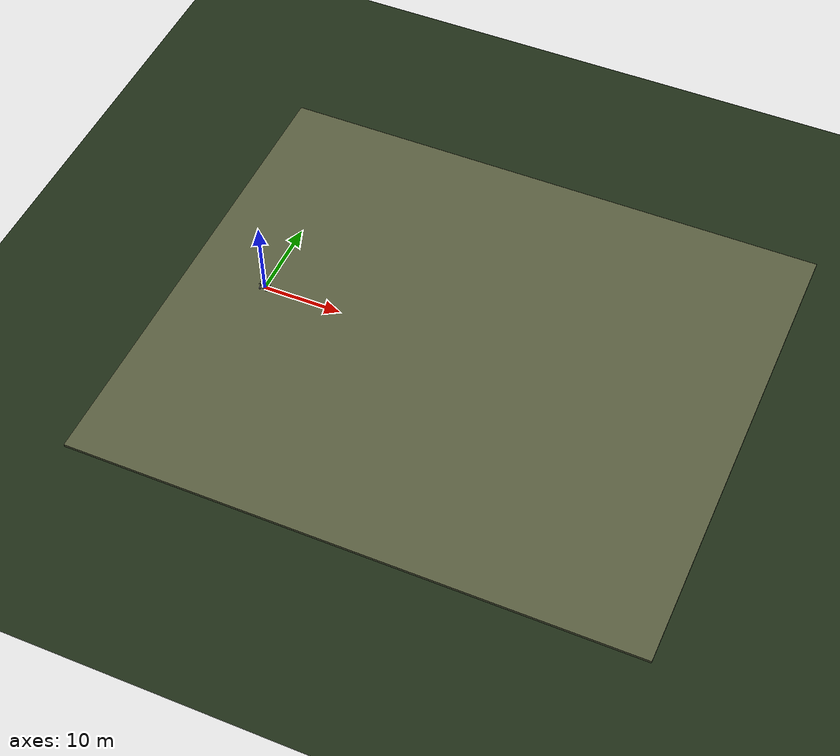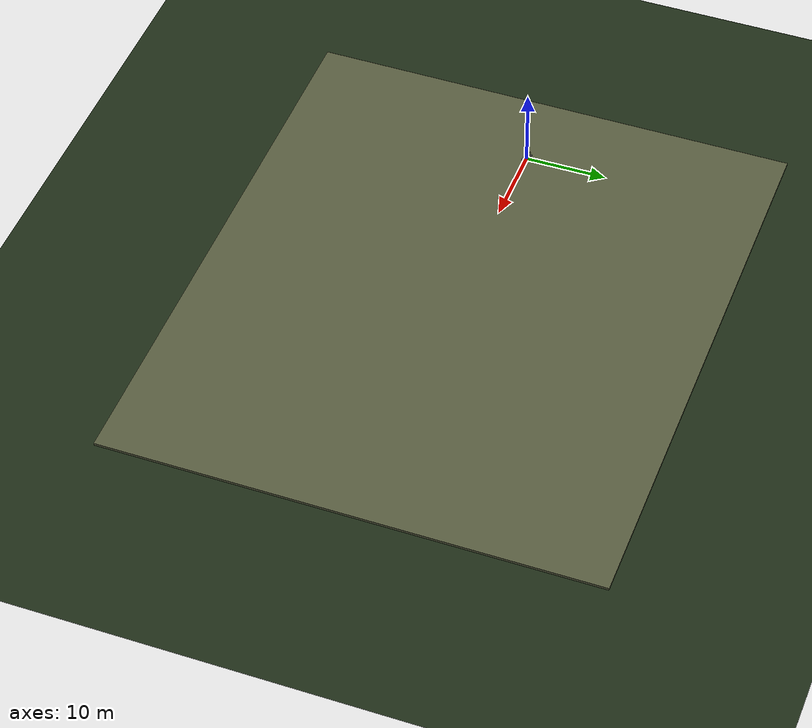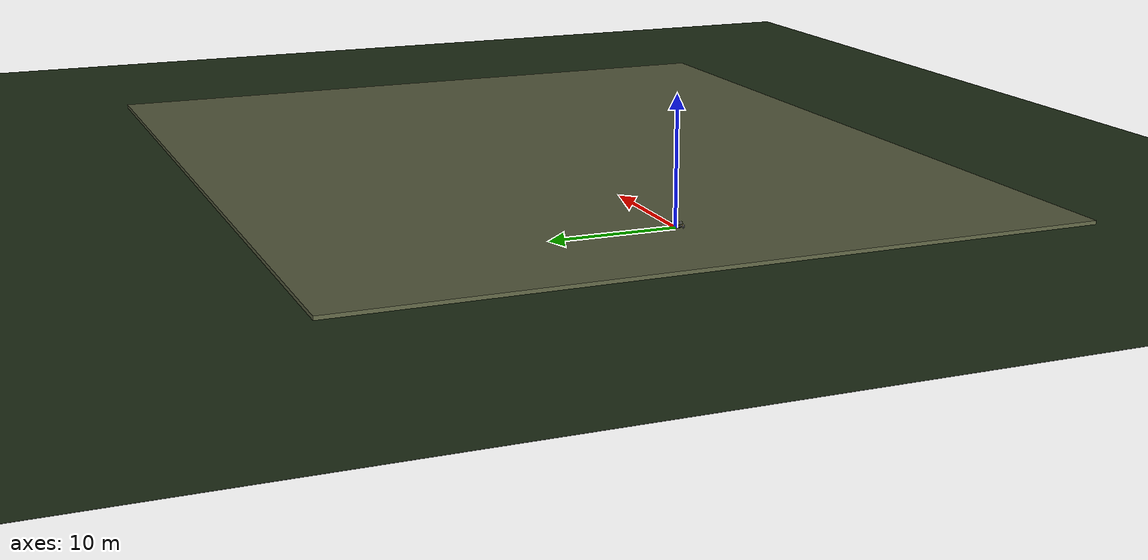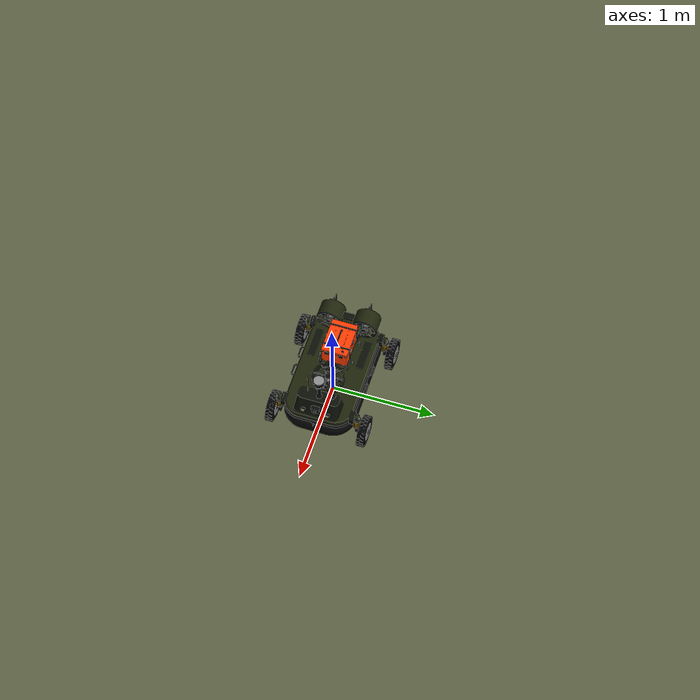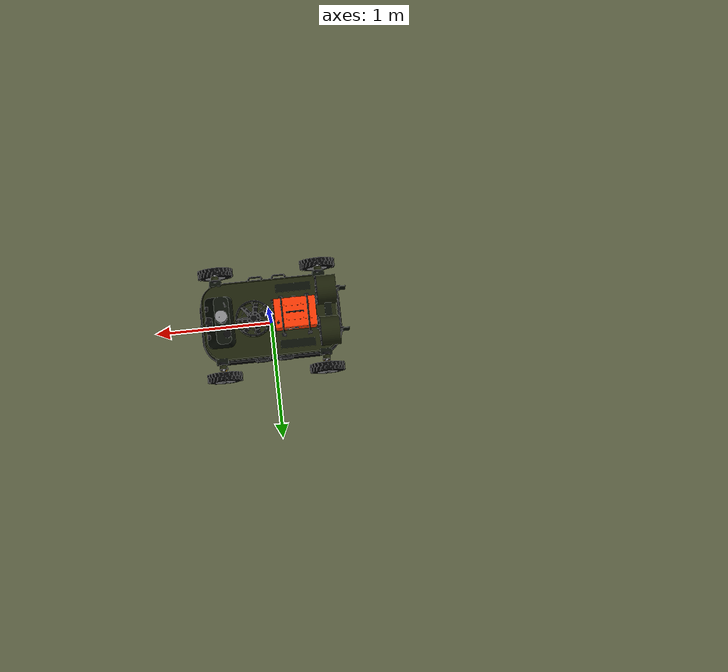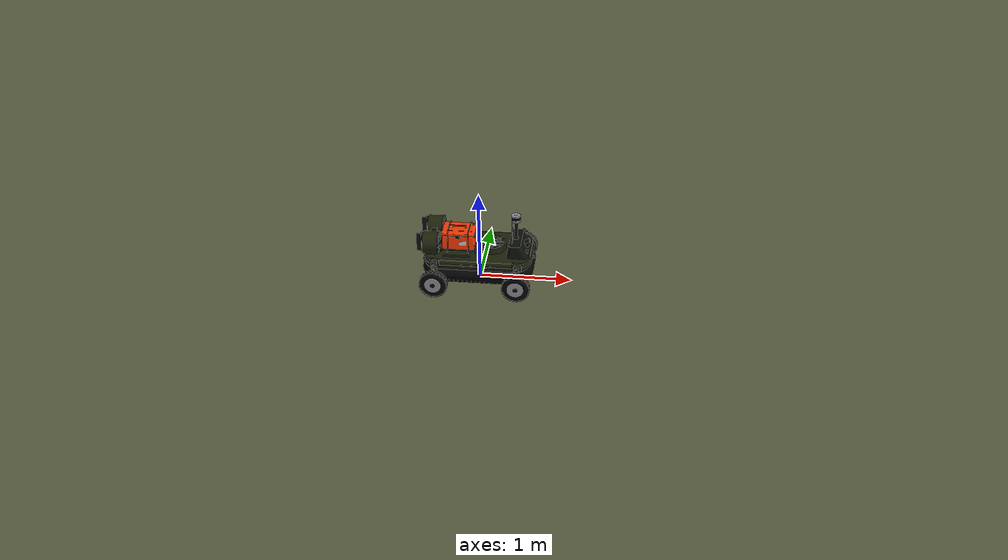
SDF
<?xml version="1.0"?>
<!-- GENERATED by hover_gazebo/scripts/gen_worlds.py -->
<sdf version="1.9">
  <world name="cmd_vel_test">
    <physics name="1ms" type="dart">
      <max_step_size>0.001</max_step_size>
      <real_time_factor>1.0</real_time_factor>
      <dart><collision_detector>bullet</collision_detector></dart>
    </physics>
    <gravity>0 0 -9.81</gravity>
    <spherical_coordinates>
      <surface_model>EARTH_WGS84</surface_model>
      <latitude_deg>1.4466</latitude_deg><longitude_deg>103.7300</longitude_deg>
      <elevation>0</elevation><heading_deg>0</heading_deg>
    </spherical_coordinates>

    <plugin filename="gz-sim-physics-system" name="gz::sim::systems::Physics"/>
    <plugin filename="gz-sim-user-commands-system" name="gz::sim::systems::UserCommands"/>
    <plugin filename="gz-sim-scene-broadcaster-system" name="gz::sim::systems::SceneBroadcaster"/>
    <plugin filename="gz-sim-imu-system" name="gz::sim::systems::Imu"/>
    <plugin filename="gz-sim-navsat-system" name="gz::sim::systems::NavSat"/>
    <plugin filename="gz-sim-sensors-system" name="gz::sim::systems::Sensors">
      <render_engine>ogre2</render_engine>
    </plugin>
    <plugin filename="tidal_vehicle_plugins" name="hover::TerrainZones">
      <ground_height>0.0</ground_height>
    </plugin>
    <plugin filename="tidal_vehicle_plugins" name="hover::ScriptedCommands">
      <command><time>0.5</time><topic>/model/hovercraft/hover_enabled</topic><type>gz.msgs.Boolean</type><data>data: true</data></command>
      <command><time>2.0</time><topic>/model/hovercraft/legs_cmd</topic><type>gz.msgs.Double</type><data>data: 1.5708</data></command>
      <command><time>4.0</time><topic>/model/hovercraft/cmd_vel_hover</topic><type>gz.msgs.Twist</type><data>linear { x: 1.5 } angular { z: 0.0 }</data></command>
      <command><time>4.1</time><topic>/model/hovercraft/cmd_vel_hover</topic><type>gz.msgs.Twist</type><data>linear { x: 1.5 } angular { z: 0.0 }</data></command>
      <command><time>4.2</time><topic>/model/hovercraft/cmd_vel_hover</topic><type>gz.msgs.Twist</type><data>linear { x: 1.5 } angular { z: 0.0 }</data></command>
      <command><time>4.3</time><topic>/model/hovercraft/cmd_vel_hover</topic><type>gz.msgs.Twist</type><data>linear { x: 1.5 } angular { z: 0.0 }</data></command>
      <command><time>4.4</time><topic>/model/hovercraft/cmd_vel_hover</topic><type>gz.msgs.Twist</type><data>linear { x: 1.5 } angular { z: 0.0 }</data></command>
      <command><time>4.5</time><topic>/model/hovercraft/cmd_vel_hover</topic><type>gz.msgs.Twist</type><data>linear { x: 1.5 } angular { z: 0.0 }</data></command>
      <command><time>4.6</time><topic>/model/hovercraft/cmd_vel_hover</topic><type>gz.msgs.Twist</type><data>linear { x: 1.5 } angular { z: 0.0 }</data></command>
      <command><time>4.7</time><topic>/model/hovercraft/cmd_vel_hover</topic><type>gz.msgs.Twist</type><data>linear { x: 1.5 } angular { z: 0.0 }</data></command>
      <command><time>4.8</time><topic>/model/hovercraft/cmd_vel_hover</topic><type>gz.msgs.Twist</type><data>linear { x: 1.5 } angular { z: 0.0 }</data></command>
      <command><time>4.9</time><topic>/model/hovercraft/cmd_vel_hover</topic><type>gz.msgs.Twist</type><data>linear { x: 1.5 } angular { z: 0.0 }</data></command>
      <command><time>5.0</time><topic>/model/hovercraft/cmd_vel_hover</topic><type>gz.msgs.Twist</type><data>linear { x: 1.5 } angular { z: 0.0 }</data></command>
      <command><time>5.1</time><topic>/model/hovercraft/cmd_vel_hover</topic><type>gz.msgs.Twist</type><data>linear { x: 1.5 } angular { z: 0.0 }</data></command>
      <command><time>5.2</time><topic>/model/hovercraft/cmd_vel_hover</topic><type>gz.msgs.Twist</type><data>linear { x: 1.5 } angular { z: 0.0 }</data></command>
      <command><time>5.3</time><topic>/model/hovercraft/cmd_vel_hover</topic><type>gz.msgs.Twist</type><data>linear { x: 1.5 } angular { z: 0.0 }</data></command>
      <command><time>5.4</time><topic>/model/hovercraft/cmd_vel_hover</topic><type>gz.msgs.Twist</type><data>linear { x: 1.5 } angular { z: 0.0 }</data></command>
      <command><time>5.5</time><topic>/model/hovercraft/cmd_vel_hover</topic><type>gz.msgs.Twist</type><data>linear { x: 1.5 } angular { z: 0.0 }</data></command>
      <command><time>5.6</time><topic>/model/hovercraft/cmd_vel_hover</topic><type>gz.msgs.Twist</type><data>linear { x: 1.5 } angular { z: 0.0 }</data></command>
      <command><time>5.7</time><topic>/model/hovercraft/cmd_vel_hover</topic><type>gz.msgs.Twist</type><data>linear { x: 1.5 } angular { z: 0.0 }</data></command>
      <command><time>5.8</time><topic>/model/hovercraft/cmd_vel_hover</topic><type>gz.msgs.Twist</type><data>linear { x: 1.5 } angular { z: 0.0 }</data></command>
      <command><time>5.9</time><topic>/model/hovercraft/cmd_vel_hover</topic><type>gz.msgs.Twist</type><data>linear { x: 1.5 } angular { z: 0.0 }</data></command>
      <command><time>6.0</time><topic>/model/hovercraft/cmd_vel_hover</topic><type>gz.msgs.Twist</type><data>linear { x: 1.5 } angular { z: 0.0 }</data></command>
      <command><time>6.1</time><topic>/model/hovercraft/cmd_vel_hover</topic><type>gz.msgs.Twist</type><data>linear { x: 1.5 } angular { z: 0.0 }</data></command>
      <command><time>6.2</time><topic>/model/hovercraft/cmd_vel_hover</topic><type>gz.msgs.Twist</type><data>linear { x: 1.5 } angular { z: 0.0 }</data></command>
      <command><time>6.3</time><topic>/model/hovercraft/cmd_vel_hover</topic><type>gz.msgs.Twist</type><data>linear { x: 1.5 } angular { z: 0.0 }</data></command>
      <command><time>6.4</time><topic>/model/hovercraft/cmd_vel_hover</topic><type>gz.msgs.Twist</type><data>linear { x: 1.5 } angular { z: 0.0 }</data></command>
      <command><time>6.5</time><topic>/model/hovercraft/cmd_vel_hover</topic><type>gz.msgs.Twist</type><data>linear { x: 1.5 } angular { z: 0.0 }</data></command>
      <command><time>6.6</time><topic>/model/hovercraft/cmd_vel_hover</topic><type>gz.msgs.Twist</type><data>linear { x: 1.5 } angular { z: 0.0 }</data></command>
      <command><time>6.7</time><topic>/model/hovercraft/cmd_vel_hover</topic><type>gz.msgs.Twist</type><data>linear { x: 1.5 } angular { z: 0.0 }</data></command>
      <command><time>6.8</time><topic>/model/hovercraft/cmd_vel_hover</topic><type>gz.msgs.Twist</type><data>linear { x: 1.5 } angular { z: 0.0 }</data></command>
      <command><time>6.9</time><topic>/model/hovercraft/cmd_vel_hover</topic><type>gz.msgs.Twist</type><data>linear { x: 1.5 } angular { z: 0.0 }</data></command>
      <command><time>7.0</time><topic>/model/hovercraft/cmd_vel_hover</topic><type>gz.msgs.Twist</type><data>linear { x: 1.5 } angular { z: 0.0 }</data></command>
      <command><time>7.1</time><topic>/model/hovercraft/cmd_vel_hover</topic><type>gz.msgs.Twist</type><data>linear { x: 1.5 } angular { z: 0.0 }</data></command>
      <command><time>7.2</time><topic>/model/hovercraft/cmd_vel_hover</topic><type>gz.msgs.Twist</type><data>linear { x: 1.5 } angular { z: 0.0 }</data></command>
      <command><time>7.3</time><topic>/model/hovercraft/cmd_vel_hover</topic><type>gz.msgs.Twist</type><data>linear { x: 1.5 } angular { z: 0.0 }</data></command>
      <command><time>7.4</time><topic>/model/hovercraft/cmd_vel_hover</topic><type>gz.msgs.Twist</type><data>linear { x: 1.5 } angular { z: 0.0 }</data></command>
      <command><time>7.5</time><topic>/model/hovercraft/cmd_vel_hover</topic><type>gz.msgs.Twist</type><data>linear { x: 1.5 } angular { z: 0.0 }</data></command>
      <command><time>7.6</time><topic>/model/hovercraft/cmd_vel_hover</topic><type>gz.msgs.Twist</type><data>linear { x: 1.5 } angular { z: 0.0 }</data></command>
      <command><time>7.7</time><topic>/model/hovercraft/cmd_vel_hover</topic><type>gz.msgs.Twist</type><data>linear { x: 1.5 } angular { z: 0.0 }</data></command>
      <command><time>7.8</time><topic>/model/hovercraft/cmd_vel_hover</topic><type>gz.msgs.Twist</type><data>linear { x: 1.5 } angular { z: 0.0 }</data></command>
      <command><time>7.9</time><topic>/model/hovercraft/cmd_vel_hover</topic><type>gz.msgs.Twist</type><data>linear { x: 1.5 } angular { z: 0.0 }</data></command>
      <command><time>8.0</time><topic>/model/hovercraft/cmd_vel_hover</topic><type>gz.msgs.Twist</type><data>linear { x: 1.5 } angular { z: 0.0 }</data></command>
      <command><time>8.1</time><topic>/model/hovercraft/cmd_vel_hover</topic><type>gz.msgs.Twist</type><data>linear { x: 1.5 } angular { z: 0.0 }</data></command>
      <command><time>8.2</time><topic>/model/hovercraft/cmd_vel_hover</topic><type>gz.msgs.Twist</type><data>linear { x: 1.5 } angular { z: 0.0 }</data></command>
      <command><time>8.3</time><topic>/model/hovercraft/cmd_vel_hover</topic><type>gz.msgs.Twist</type><data>linear { x: 1.5 } angular { z: 0.0 }</data></command>
      <command><time>8.4</time><topic>/model/hovercraft/cmd_vel_hover</topic><type>gz.msgs.Twist</type><data>linear { x: 1.5 } angular { z: 0.0 }</data></command>
      <command><time>8.5</time><topic>/model/hovercraft/cmd_vel_hover</topic><type>gz.msgs.Twist</type><data>linear { x: 1.5 } angular { z: 0.0 }</data></command>
      <command><time>8.6</time><topic>/model/hovercraft/cmd_vel_hover</topic><type>gz.msgs.Twist</type><data>linear { x: 1.5 } angular { z: 0.0 }</data></command>
      <command><time>8.7</time><topic>/model/hovercraft/cmd_vel_hover</topic><type>gz.msgs.Twist</type><data>linear { x: 1.5 } angular { z: 0.0 }</data></command>
      <command><time>8.8</time><topic>/model/hovercraft/cmd_vel_hover</topic><type>gz.msgs.Twist</type><data>linear { x: 1.5 } angular { z: 0.0 }</data></command>
      <command><time>8.9</time><topic>/model/hovercraft/cmd_vel_hover</topic><type>gz.msgs.Twist</type><data>linear { x: 1.5 } angular { z: 0.0 }</data></command>
      <command><time>9.0</time><topic>/model/hovercraft/cmd_vel_hover</topic><type>gz.msgs.Twist</type><data>linear { x: 1.5 } angular { z: 0.0 }</data></command>
      <command><time>9.1</time><topic>/model/hovercraft/cmd_vel_hover</topic><type>gz.msgs.Twist</type><data>linear { x: 1.5 } angular { z: 0.0 }</data></command>
      <command><time>9.2</time><topic>/model/hovercraft/cmd_vel_hover</topic><type>gz.msgs.Twist</type><data>linear { x: 1.5 } angular { z: 0.0 }</data></command>
      <command><time>9.3</time><topic>/model/hovercraft/cmd_vel_hover</topic><type>gz.msgs.Twist</type><data>linear { x: 1.5 } angular { z: 0.0 }</data></command>
      <command><time>9.4</time><topic>/model/hovercraft/cmd_vel_hover</topic><type>gz.msgs.Twist</type><data>linear { x: 1.5 } angular { z: 0.0 }</data></command>
      <command><time>9.5</time><topic>/model/hovercraft/cmd_vel_hover</topic><type>gz.msgs.Twist</type><data>linear { x: 1.5 } angular { z: 0.0 }</data></command>
      <command><time>9.6</time><topic>/model/hovercraft/cmd_vel_hover</topic><type>gz.msgs.Twist</type><data>linear { x: 1.5 } angular { z: 0.0 }</data></command>
      <command><time>9.7</time><topic>/model/hovercraft/cmd_vel_hover</topic><type>gz.msgs.Twist</type><data>linear { x: 1.5 } angular { z: 0.0 }</data></command>
      <command><time>9.8</time><topic>/model/hovercraft/cmd_vel_hover</topic><type>gz.msgs.Twist</type><data>linear { x: 1.5 } angular { z: 0.0 }</data></command>
      <command><time>9.9</time><topic>/model/hovercraft/cmd_vel_hover</topic><type>gz.msgs.Twist</type><data>linear { x: 1.5 } angular { z: 0.0 }</data></command>
      <command><time>10.0</time><topic>/model/hovercraft/cmd_vel_hover</topic><type>gz.msgs.Twist</type><data>linear { x: 1.5 } angular { z: 0.0 }</data></command>
      <command><time>10.1</time><topic>/model/hovercraft/cmd_vel_hover</topic><type>gz.msgs.Twist</type><data>linear { x: 1.5 } angular { z: 0.0 }</data></command>
      <command><time>10.2</time><topic>/model/hovercraft/cmd_vel_hover</topic><type>gz.msgs.Twist</type><data>linear { x: 1.5 } angular { z: 0.0 }</data></command>
      <command><time>10.3</time><topic>/model/hovercraft/cmd_vel_hover</topic><type>gz.msgs.Twist</type><data>linear { x: 1.5 } angular { z: 0.0 }</data></command>
      <command><time>10.4</time><topic>/model/hovercraft/cmd_vel_hover</topic><type>gz.msgs.Twist</type><data>linear { x: 1.5 } angular { z: 0.0 }</data></command>
      <command><time>10.5</time><topic>/model/hovercraft/cmd_vel_hover</topic><type>gz.msgs.Twist</type><data>linear { x: 1.5 } angular { z: 0.0 }</data></command>
      <command><time>10.6</time><topic>/model/hovercraft/cmd_vel_hover</topic><type>gz.msgs.Twist</type><data>linear { x: 1.5 } angular { z: 0.0 }</data></command>
      <command><time>10.7</time><topic>/model/hovercraft/cmd_vel_hover</topic><type>gz.msgs.Twist</type><data>linear { x: 1.5 } angular { z: 0.0 }</data></command>
      <command><time>10.8</time><topic>/model/hovercraft/cmd_vel_hover</topic><type>gz.msgs.Twist</type><data>linear { x: 1.5 } angular { z: 0.0 }</data></command>
      <command><time>10.9</time><topic>/model/hovercraft/cmd_vel_hover</topic><type>gz.msgs.Twist</type><data>linear { x: 1.5 } angular { z: 0.0 }</data></command>
      <command><time>11.0</time><topic>/model/hovercraft/cmd_vel_hover</topic><type>gz.msgs.Twist</type><data>linear { x: 1.5 } angular { z: 0.0 }</data></command>
      <command><time>11.1</time><topic>/model/hovercraft/cmd_vel_hover</topic><type>gz.msgs.Twist</type><data>linear { x: 1.5 } angular { z: 0.0 }</data></command>
      <command><time>11.2</time><topic>/model/hovercraft/cmd_vel_hover</topic><type>gz.msgs.Twist</type><data>linear { x: 1.5 } angular { z: 0.0 }</data></command>
      <command><time>11.3</time><topic>/model/hovercraft/cmd_vel_hover</topic><type>gz.msgs.Twist</type><data>linear { x: 1.5 } angular { z: 0.0 }</data></command>
      <command><time>11.4</time><topic>/model/hovercraft/cmd_vel_hover</topic><type>gz.msgs.Twist</type><data>linear { x: 1.5 } angular { z: 0.0 }</data></command>
      <command><time>11.5</time><topic>/model/hovercraft/cmd_vel_hover</topic><type>gz.msgs.Twist</type><data>linear { x: 1.5 } angular { z: 0.0 }</data></command>
      <command><time>11.6</time><topic>/model/hovercraft/cmd_vel_hover</topic><type>gz.msgs.Twist</type><data>linear { x: 1.5 } angular { z: 0.0 }</data></command>
      <command><time>11.7</time><topic>/model/hovercraft/cmd_vel_hover</topic><type>gz.msgs.Twist</type><data>linear { x: 1.5 } angular { z: 0.0 }</data></command>
      <command><time>11.8</time><topic>/model/hovercraft/cmd_vel_hover</topic><type>gz.msgs.Twist</type><data>linear { x: 1.5 } angular { z: 0.0 }</data></command>
      <command><time>11.9</time><topic>/model/hovercraft/cmd_vel_hover</topic><type>gz.msgs.Twist</type><data>linear { x: 1.5 } angular { z: 0.0 }</data></command>
      <command><time>12.0</time><topic>/model/hovercraft/cmd_vel_hover</topic><type>gz.msgs.Twist</type><data>linear { x: 1.5 } angular { z: 0.0 }</data></command>
      <command><time>12.1</time><topic>/model/hovercraft/cmd_vel_hover</topic><type>gz.msgs.Twist</type><data>linear { x: 1.0 } angular { z: 0.5 }</data></command>
      <command><time>12.2</time><topic>/model/hovercraft/cmd_vel_hover</topic><type>gz.msgs.Twist</type><data>linear { x: 1.0 } angular { z: 0.5 }</data></command>
      <command><time>12.3</time><topic>/model/hovercraft/cmd_vel_hover</topic><type>gz.msgs.Twist</type><data>linear { x: 1.0 } angular { z: 0.5 }</data></command>
      <command><time>12.4</time><topic>/model/hovercraft/cmd_vel_hover</topic><type>gz.msgs.Twist</type><data>linear { x: 1.0 } angular { z: 0.5 }</data></command>
      <command><time>12.5</time><topic>/model/hovercraft/cmd_vel_hover</topic><type>gz.msgs.Twist</type><data>linear { x: 1.0 } angular { z: 0.5 }</data></command>
      <command><time>12.6</time><topic>/model/hovercraft/cmd_vel_hover</topic><type>gz.msgs.Twist</type><data>linear { x: 1.0 } angular { z: 0.5 }</data></command>
      <command><time>12.7</time><topic>/model/hovercraft/cmd_vel_hover</topic><type>gz.msgs.Twist</type><data>linear { x: 1.0 } angular { z: 0.5 }</data></command>
      <command><time>12.8</time><topic>/model/hovercraft/cmd_vel_hover</topic><type>gz.msgs.Twist</type><data>linear { x: 1.0 } angular { z: 0.5 }</data></command>
      <command><time>12.9</time><topic>/model/hovercraft/cmd_vel_hover</topic><type>gz.msgs.Twist</type><data>linear { x: 1.0 } angular { z: 0.5 }</data></command>
      <command><time>13.0</time><topic>/model/hovercraft/cmd_vel_hover</topic><type>gz.msgs.Twist</type><data>linear { x: 1.0 } angular { z: 0.5 }</data></command>
      <command><time>13.1</time><topic>/model/hovercraft/cmd_vel_hover</topic><type>gz.msgs.Twist</type><data>linear { x: 1.0 } angular { z: 0.5 }</data></command>
      <command><time>13.2</time><topic>/model/hovercraft/cmd_vel_hover</topic><type>gz.msgs.Twist</type><data>linear { x: 1.0 } angular { z: 0.5 }</data></command>
      <command><time>13.3</time><topic>/model/hovercraft/cmd_vel_hover</topic><type>gz.msgs.Twist</type><data>linear { x: 1.0 } angular { z: 0.5 }</data></command>
      <command><time>13.4</time><topic>/model/hovercraft/cmd_vel_hover</topic><type>gz.msgs.Twist</type><data>linear { x: 1.0 } angular { z: 0.5 }</data></command>
      <command><time>13.5</time><topic>/model/hovercraft/cmd_vel_hover</topic><type>gz.msgs.Twist</type><data>linear { x: 1.0 } angular { z: 0.5 }</data></command>
      <command><time>13.6</time><topic>/model/hovercraft/cmd_vel_hover</topic><type>gz.msgs.Twist</type><data>linear { x: 1.0 } angular { z: 0.5 }</data></command>
      <command><time>13.7</time><topic>/model/hovercraft/cmd_vel_hover</topic><type>gz.msgs.Twist</type><data>linear { x: 1.0 } angular { z: 0.5 }</data></command>
      <command><time>13.8</time><topic>/model/hovercraft/cmd_vel_hover</topic><type>gz.msgs.Twist</type><data>linear { x: 1.0 } angular { z: 0.5 }</data></command>
      <command><time>13.9</time><topic>/model/hovercraft/cmd_vel_hover</topic><type>gz.msgs.Twist</type><data>linear { x: 1.0 } angular { z: 0.5 }</data></command>
      <command><time>14.0</time><topic>/model/hovercraft/cmd_vel_hover</topic><type>gz.msgs.Twist</type><data>linear { x: 1.0 } angular { z: 0.5 }</data></command>
      <command><time>14.1</time><topic>/model/hovercraft/cmd_vel_hover</topic><type>gz.msgs.Twist</type><data>linear { x: 1.0 } angular { z: 0.5 }</data></command>
      <command><time>14.2</time><topic>/model/hovercraft/cmd_vel_hover</topic><type>gz.msgs.Twist</type><data>linear { x: 1.0 } angular { z: 0.5 }</data></command>
      <command><time>14.3</time><topic>/model/hovercraft/cmd_vel_hover</topic><type>gz.msgs.Twist</type><data>linear { x: 1.0 } angular { z: 0.5 }</data></command>
      <command><time>14.4</time><topic>/model/hovercraft/cmd_vel_hover</topic><type>gz.msgs.Twist</type><data>linear { x: 1.0 } angular { z: 0.5 }</data></command>
      <command><time>14.5</time><topic>/model/hovercraft/cmd_vel_hover</topic><type>gz.msgs.Twist</type><data>linear { x: 1.0 } angular { z: 0.5 }</data></command>
      <command><time>14.6</time><topic>/model/hovercraft/cmd_vel_hover</topic><type>gz.msgs.Twist</type><data>linear { x: 1.0 } angular { z: 0.5 }</data></command>
      <command><time>14.7</time><topic>/model/hovercraft/cmd_vel_hover</topic><type>gz.msgs.Twist</type><data>linear { x: 1.0 } angular { z: 0.5 }</data></command>
      <command><time>14.8</time><topic>/model/hovercraft/cmd_vel_hover</topic><type>gz.msgs.Twist</type><data>linear { x: 1.0 } angular { z: 0.5 }</data></command>
      <command><time>14.9</time><topic>/model/hovercraft/cmd_vel_hover</topic><type>gz.msgs.Twist</type><data>linear { x: 1.0 } angular { z: 0.5 }</data></command>
      <command><time>15.0</time><topic>/model/hovercraft/cmd_vel_hover</topic><type>gz.msgs.Twist</type><data>linear { x: 1.0 } angular { z: 0.5 }</data></command>
      <command><time>15.1</time><topic>/model/hovercraft/cmd_vel_hover</topic><type>gz.msgs.Twist</type><data>linear { x: 1.0 } angular { z: 0.5 }</data></command>
      <command><time>15.2</time><topic>/model/hovercraft/cmd_vel_hover</topic><type>gz.msgs.Twist</type><data>linear { x: 1.0 } angular { z: 0.5 }</data></command>
      <command><time>15.3</time><topic>/model/hovercraft/cmd_vel_hover</topic><type>gz.msgs.Twist</type><data>linear { x: 1.0 } angular { z: 0.5 }</data></command>
      <command><time>15.4</time><topic>/model/hovercraft/cmd_vel_hover</topic><type>gz.msgs.Twist</type><data>linear { x: 1.0 } angular { z: 0.5 }</data></command>
      <command><time>15.5</time><topic>/model/hovercraft/cmd_vel_hover</topic><type>gz.msgs.Twist</type><data>linear { x: 1.0 } angular { z: 0.5 }</data></command>
      <command><time>15.6</time><topic>/model/hovercraft/cmd_vel_hover</topic><type>gz.msgs.Twist</type><data>linear { x: 1.0 } angular { z: 0.5 }</data></command>
      <command><time>15.7</time><topic>/model/hovercraft/cmd_vel_hover</topic><type>gz.msgs.Twist</type><data>linear { x: 1.0 } angular { z: 0.5 }</data></command>
      <command><time>15.8</time><topic>/model/hovercraft/cmd_vel_hover</topic><type>gz.msgs.Twist</type><data>linear { x: 1.0 } angular { z: 0.5 }</data></command>
      <command><time>15.9</time><topic>/model/hovercraft/cmd_vel_hover</topic><type>gz.msgs.Twist</type><data>linear { x: 1.0 } angular { z: 0.5 }</data></command>
      <command><time>16.0</time><topic>/model/hovercraft/cmd_vel_hover</topic><type>gz.msgs.Twist</type><data>linear { x: 1.0 } angular { z: 0.5 }</data></command>
      <command><time>16.1</time><topic>/model/hovercraft/cmd_vel_hover</topic><type>gz.msgs.Twist</type><data>linear { x: 1.0 } angular { z: 0.5 }</data></command>
      <command><time>16.2</time><topic>/model/hovercraft/cmd_vel_hover</topic><type>gz.msgs.Twist</type><data>linear { x: 1.0 } angular { z: 0.5 }</data></command>
      <command><time>16.3</time><topic>/model/hovercraft/cmd_vel_hover</topic><type>gz.msgs.Twist</type><data>linear { x: 1.0 } angular { z: 0.5 }</data></command>
      <command><time>16.4</time><topic>/model/hovercraft/cmd_vel_hover</topic><type>gz.msgs.Twist</type><data>linear { x: 1.0 } angular { z: 0.5 }</data></command>
      <command><time>16.5</time><topic>/model/hovercraft/cmd_vel_hover</topic><type>gz.msgs.Twist</type><data>linear { x: 1.0 } angular { z: 0.5 }</data></command>
      <command><time>16.6</time><topic>/model/hovercraft/cmd_vel_hover</topic><type>gz.msgs.Twist</type><data>linear { x: 1.0 } angular { z: 0.5 }</data></command>
      <command><time>16.7</time><topic>/model/hovercraft/cmd_vel_hover</topic><type>gz.msgs.Twist</type><data>linear { x: 1.0 } angular { z: 0.5 }</data></command>
      <command><time>16.8</time><topic>/model/hovercraft/cmd_vel_hover</topic><type>gz.msgs.Twist</type><data>linear { x: 1.0 } angular { z: 0.5 }</data></command>
      <command><time>16.9</time><topic>/model/hovercraft/cmd_vel_hover</topic><type>gz.msgs.Twist</type><data>linear { x: 1.0 } angular { z: 0.5 }</data></command>
      <command><time>17.0</time><topic>/model/hovercraft/cmd_vel_hover</topic><type>gz.msgs.Twist</type><data>linear { x: 1.0 } angular { z: 0.5 }</data></command>
      <command><time>17.1</time><topic>/model/hovercraft/cmd_vel_hover</topic><type>gz.msgs.Twist</type><data>linear { x: 1.0 } angular { z: 0.5 }</data></command>
      <command><time>17.2</time><topic>/model/hovercraft/cmd_vel_hover</topic><type>gz.msgs.Twist</type><data>linear { x: 1.0 } angular { z: 0.5 }</data></command>
      <command><time>17.3</time><topic>/model/hovercraft/cmd_vel_hover</topic><type>gz.msgs.Twist</type><data>linear { x: 1.0 } angular { z: 0.5 }</data></command>
      <command><time>17.4</time><topic>/model/hovercraft/cmd_vel_hover</topic><type>gz.msgs.Twist</type><data>linear { x: 1.0 } angular { z: 0.5 }</data></command>
      <command><time>17.5</time><topic>/model/hovercraft/cmd_vel_hover</topic><type>gz.msgs.Twist</type><data>linear { x: 1.0 } angular { z: 0.5 }</data></command>
      <command><time>17.6</time><topic>/model/hovercraft/cmd_vel_hover</topic><type>gz.msgs.Twist</type><data>linear { x: 1.0 } angular { z: 0.5 }</data></command>
      <command><time>17.7</time><topic>/model/hovercraft/cmd_vel_hover</topic><type>gz.msgs.Twist</type><data>linear { x: 1.0 } angular { z: 0.5 }</data></command>
      <command><time>17.8</time><topic>/model/hovercraft/cmd_vel_hover</topic><type>gz.msgs.Twist</type><data>linear { x: 1.0 } angular { z: 0.5 }</data></command>
      <command><time>17.9</time><topic>/model/hovercraft/cmd_vel_hover</topic><type>gz.msgs.Twist</type><data>linear { x: 1.0 } angular { z: 0.5 }</data></command>
      <command><time>18.0</time><topic>/model/hovercraft/cmd_vel_hover</topic><type>gz.msgs.Twist</type><data>linear { x: 1.0 } angular { z: 0.5 }</data></command>
      <command><time>18.1</time><topic>/model/hovercraft/cmd_vel_hover</topic><type>gz.msgs.Twist</type><data>linear { x: 1.0 } angular { z: 0.5 }</data></command>
      <command><time>18.2</time><topic>/model/hovercraft/cmd_vel_hover</topic><type>gz.msgs.Twist</type><data>linear { x: 1.0 } angular { z: 0.5 }</data></command>
      <command><time>18.3</time><topic>/model/hovercraft/cmd_vel_hover</topic><type>gz.msgs.Twist</type><data>linear { x: 1.0 } angular { z: 0.5 }</data></command>
      <command><time>18.4</time><topic>/model/hovercraft/cmd_vel_hover</topic><type>gz.msgs.Twist</type><data>linear { x: 1.0 } angular { z: 0.5 }</data></command>
      <command><time>18.5</time><topic>/model/hovercraft/cmd_vel_hover</topic><type>gz.msgs.Twist</type><data>linear { x: 1.0 } angular { z: 0.5 }</data></command>
      <command><time>18.6</time><topic>/model/hovercraft/cmd_vel_hover</topic><type>gz.msgs.Twist</type><data>linear { x: 1.0 } angular { z: 0.5 }</data></command>
      <command><time>18.7</time><topic>/model/hovercraft/cmd_vel_hover</topic><type>gz.msgs.Twist</type><data>linear { x: 1.0 } angular { z: 0.5 }</data></command>
      <command><time>18.8</time><topic>/model/hovercraft/cmd_vel_hover</topic><type>gz.msgs.Twist</type><data>linear { x: 1.0 } angular { z: 0.5 }</data></command>
      <command><time>18.9</time><topic>/model/hovercraft/cmd_vel_hover</topic><type>gz.msgs.Twist</type><data>linear { x: 1.0 } angular { z: 0.5 }</data></command>
      <command><time>19.0</time><topic>/model/hovercraft/cmd_vel_hover</topic><type>gz.msgs.Twist</type><data>linear { x: 1.0 } angular { z: 0.5 }</data></command>
      <command><time>19.1</time><topic>/model/hovercraft/cmd_vel_hover</topic><type>gz.msgs.Twist</type><data>linear { x: 1.0 } angular { z: 0.5 }</data></command>
      <command><time>19.2</time><topic>/model/hovercraft/cmd_vel_hover</topic><type>gz.msgs.Twist</type><data>linear { x: 1.0 } angular { z: 0.5 }</data></command>
      <command><time>19.3</time><topic>/model/hovercraft/cmd_vel_hover</topic><type>gz.msgs.Twist</type><data>linear { x: 1.0 } angular { z: 0.5 }</data></command>
      <command><time>19.4</time><topic>/model/hovercraft/cmd_vel_hover</topic><type>gz.msgs.Twist</type><data>linear { x: 1.0 } angular { z: 0.5 }</data></command>
      <command><time>19.5</time><topic>/model/hovercraft/cmd_vel_hover</topic><type>gz.msgs.Twist</type><data>linear { x: 1.0 } angular { z: 0.5 }</data></command>
      <command><time>19.6</time><topic>/model/hovercraft/cmd_vel_hover</topic><type>gz.msgs.Twist</type><data>linear { x: 1.0 } angular { z: 0.5 }</data></command>
      <command><time>19.7</time><topic>/model/hovercraft/cmd_vel_hover</topic><type>gz.msgs.Twist</type><data>linear { x: 1.0 } angular { z: 0.5 }</data></command>
      <command><time>19.8</time><topic>/model/hovercraft/cmd_vel_hover</topic><type>gz.msgs.Twist</type><data>linear { x: 1.0 } angular { z: 0.5 }</data></command>
      <command><time>19.9</time><topic>/model/hovercraft/cmd_vel_hover</topic><type>gz.msgs.Twist</type><data>linear { x: 1.0 } angular { z: 0.5 }</data></command>
      <command><time>20.0</time><topic>/model/hovercraft/cmd_vel_hover</topic><type>gz.msgs.Twist</type><data>linear { x: 0.0 } angular { z: 0.0 }</data></command>
      <command><time>20.1</time><topic>/model/hovercraft/cmd_vel_hover</topic><type>gz.msgs.Twist</type><data>linear { x: 0.0 } angular { z: 0.0 }</data></command>
      <command><time>20.2</time><topic>/model/hovercraft/cmd_vel_hover</topic><type>gz.msgs.Twist</type><data>linear { x: 0.0 } angular { z: 0.0 }</data></command>
      <command><time>20.3</time><topic>/model/hovercraft/cmd_vel_hover</topic><type>gz.msgs.Twist</type><data>linear { x: 0.0 } angular { z: 0.0 }</data></command>
      <command><time>20.4</time><topic>/model/hovercraft/cmd_vel_hover</topic><type>gz.msgs.Twist</type><data>linear { x: 0.0 } angular { z: 0.0 }</data></command>
      <command><time>20.5</time><topic>/model/hovercraft/cmd_vel_hover</topic><type>gz.msgs.Twist</type><data>linear { x: 0.0 } angular { z: 0.0 }</data></command>
      <command><time>20.6</time><topic>/model/hovercraft/cmd_vel_hover</topic><type>gz.msgs.Twist</type><data>linear { x: 0.0 } angular { z: 0.0 }</data></command>
      <command><time>20.7</time><topic>/model/hovercraft/cmd_vel_hover</topic><type>gz.msgs.Twist</type><data>linear { x: 0.0 } angular { z: 0.0 }</data></command>
      <command><time>20.8</time><topic>/model/hovercraft/cmd_vel_hover</topic><type>gz.msgs.Twist</type><data>linear { x: 0.0 } angular { z: 0.0 }</data></command>
      <command><time>20.9</time><topic>/model/hovercraft/cmd_vel_hover</topic><type>gz.msgs.Twist</type><data>linear { x: 0.0 } angular { z: 0.0 }</data></command>
      <command><time>21.0</time><topic>/model/hovercraft/cmd_vel_hover</topic><type>gz.msgs.Twist</type><data>linear { x: 0.0 } angular { z: 0.0 }</data></command>
      <command><time>21.1</time><topic>/model/hovercraft/cmd_vel_hover</topic><type>gz.msgs.Twist</type><data>linear { x: 0.0 } angular { z: 0.0 }</data></command>
      <command><time>21.2</time><topic>/model/hovercraft/cmd_vel_hover</topic><type>gz.msgs.Twist</type><data>linear { x: 0.0 } angular { z: 0.0 }</data></command>
      <command><time>21.3</time><topic>/model/hovercraft/cmd_vel_hover</topic><type>gz.msgs.Twist</type><data>linear { x: 0.0 } angular { z: 0.0 }</data></command>
      <command><time>21.4</time><topic>/model/hovercraft/cmd_vel_hover</topic><type>gz.msgs.Twist</type><data>linear { x: 0.0 } angular { z: 0.0 }</data></command>
      <command><time>21.5</time><topic>/model/hovercraft/cmd_vel_hover</topic><type>gz.msgs.Twist</type><data>linear { x: 0.0 } angular { z: 0.0 }</data></command>
      <command><time>21.6</time><topic>/model/hovercraft/cmd_vel_hover</topic><type>gz.msgs.Twist</type><data>linear { x: 0.0 } angular { z: 0.0 }</data></command>
      <command><time>21.7</time><topic>/model/hovercraft/cmd_vel_hover</topic><type>gz.msgs.Twist</type><data>linear { x: 0.0 } angular { z: 0.0 }</data></command>
      <command><time>21.8</time><topic>/model/hovercraft/cmd_vel_hover</topic><type>gz.msgs.Twist</type><data>linear { x: 0.0 } angular { z: 0.0 }</data></command>
      <command><time>21.9</time><topic>/model/hovercraft/cmd_vel_hover</topic><type>gz.msgs.Twist</type><data>linear { x: 0.0 } angular { z: 0.0 }</data></command>
      <command><time>22.0</time><topic>/model/hovercraft/cmd_vel_hover</topic><type>gz.msgs.Twist</type><data>linear { x: 0.0 } angular { z: 0.0 }</data></command>
      <command><time>22.1</time><topic>/model/hovercraft/cmd_vel_hover</topic><type>gz.msgs.Twist</type><data>linear { x: 0.0 } angular { z: 0.0 }</data></command>
      <command><time>22.2</time><topic>/model/hovercraft/cmd_vel_hover</topic><type>gz.msgs.Twist</type><data>linear { x: 0.0 } angular { z: 0.0 }</data></command>
      <command><time>22.3</time><topic>/model/hovercraft/cmd_vel_hover</topic><type>gz.msgs.Twist</type><data>linear { x: 0.0 } angular { z: 0.0 }</data></command>
      <command><time>22.4</time><topic>/model/hovercraft/cmd_vel_hover</topic><type>gz.msgs.Twist</type><data>linear { x: 0.0 } angular { z: 0.0 }</data></command>
      <command><time>22.5</time><topic>/model/hovercraft/cmd_vel_hover</topic><type>gz.msgs.Twist</type><data>linear { x: 0.0 } angular { z: 0.0 }</data></command>
      <command><time>22.6</time><topic>/model/hovercraft/cmd_vel_hover</topic><type>gz.msgs.Twist</type><data>linear { x: 0.0 } angular { z: 0.0 }</data></command>
      <command><time>22.7</time><topic>/model/hovercraft/cmd_vel_hover</topic><type>gz.msgs.Twist</type><data>linear { x: 0.0 } angular { z: 0.0 }</data></command>
      <command><time>22.8</time><topic>/model/hovercraft/cmd_vel_hover</topic><type>gz.msgs.Twist</type><data>linear { x: 0.0 } angular { z: 0.0 }</data></command>
      <command><time>22.9</time><topic>/model/hovercraft/cmd_vel_hover</topic><type>gz.msgs.Twist</type><data>linear { x: 0.0 } angular { z: 0.0 }</data></command>
      <command><time>23.0</time><topic>/model/hovercraft/cmd_vel_hover</topic><type>gz.msgs.Twist</type><data>linear { x: 0.0 } angular { z: 0.0 }</data></command>
      <command><time>23.1</time><topic>/model/hovercraft/cmd_vel_hover</topic><type>gz.msgs.Twist</type><data>linear { x: 0.0 } angular { z: 0.0 }</data></command>
      <command><time>23.2</time><topic>/model/hovercraft/cmd_vel_hover</topic><type>gz.msgs.Twist</type><data>linear { x: 0.0 } angular { z: 0.0 }</data></command>
      <command><time>23.3</time><topic>/model/hovercraft/cmd_vel_hover</topic><type>gz.msgs.Twist</type><data>linear { x: 0.0 } angular { z: 0.0 }</data></command>
      <command><time>23.4</time><topic>/model/hovercraft/cmd_vel_hover</topic><type>gz.msgs.Twist</type><data>linear { x: 0.0 } angular { z: 0.0 }</data></command>
      <command><time>23.5</time><topic>/model/hovercraft/cmd_vel_hover</topic><type>gz.msgs.Twist</type><data>linear { x: 0.0 } angular { z: 0.0 }</data></command>
      <command><time>23.6</time><topic>/model/hovercraft/cmd_vel_hover</topic><type>gz.msgs.Twist</type><data>linear { x: 0.0 } angular { z: 0.0 }</data></command>
      <command><time>23.7</time><topic>/model/hovercraft/cmd_vel_hover</topic><type>gz.msgs.Twist</type><data>linear { x: 0.0 } angular { z: 0.0 }</data></command>
      <command><time>23.8</time><topic>/model/hovercraft/cmd_vel_hover</topic><type>gz.msgs.Twist</type><data>linear { x: 0.0 } angular { z: 0.0 }</data></command>
      <command><time>23.9</time><topic>/model/hovercraft/cmd_vel_hover</topic><type>gz.msgs.Twist</type><data>linear { x: 0.0 } angular { z: 0.0 }</data></command>
      <command><time>24.0</time><topic>/model/hovercraft/cmd_vel_hover</topic><type>gz.msgs.Twist</type><data>linear { x: 0.0 } angular { z: 0.0 }</data></command>
      <command><time>24.1</time><topic>/model/hovercraft/cmd_vel_hover</topic><type>gz.msgs.Twist</type><data>linear { x: 0.0 } angular { z: 0.0 }</data></command>
      <command><time>24.2</time><topic>/model/hovercraft/cmd_vel_hover</topic><type>gz.msgs.Twist</type><data>linear { x: 0.0 } angular { z: 0.0 }</data></command>
      <command><time>24.3</time><topic>/model/hovercraft/cmd_vel_hover</topic><type>gz.msgs.Twist</type><data>linear { x: 0.0 } angular { z: 0.0 }</data></command>
      <command><time>24.4</time><topic>/model/hovercraft/cmd_vel_hover</topic><type>gz.msgs.Twist</type><data>linear { x: 0.0 } angular { z: 0.0 }</data></command>
      <command><time>24.5</time><topic>/model/hovercraft/cmd_vel_hover</topic><type>gz.msgs.Twist</type><data>linear { x: 0.0 } angular { z: 0.0 }</data></command>
      <command><time>24.6</time><topic>/model/hovercraft/cmd_vel_hover</topic><type>gz.msgs.Twist</type><data>linear { x: 0.0 } angular { z: 0.0 }</data></command>
      <command><time>24.7</time><topic>/model/hovercraft/cmd_vel_hover</topic><type>gz.msgs.Twist</type><data>linear { x: 0.0 } angular { z: 0.0 }</data></command>
      <command><time>24.8</time><topic>/model/hovercraft/cmd_vel_hover</topic><type>gz.msgs.Twist</type><data>linear { x: 0.0 } angular { z: 0.0 }</data></command>
      <command><time>24.9</time><topic>/model/hovercraft/cmd_vel_hover</topic><type>gz.msgs.Twist</type><data>linear { x: 0.0 } angular { z: 0.0 }</data></command>
      <command><time>25.0</time><topic>/model/hovercraft/cmd_vel_hover</topic><type>gz.msgs.Twist</type><data>linear { x: 0.0 } angular { z: 0.0 }</data></command>
      <command><time>25.1</time><topic>/model/hovercraft/cmd_vel_hover</topic><type>gz.msgs.Twist</type><data>linear { x: 0.0 } angular { z: 0.0 }</data></command>
      <command><time>25.2</time><topic>/model/hovercraft/cmd_vel_hover</topic><type>gz.msgs.Twist</type><data>linear { x: 0.0 } angular { z: 0.0 }</data></command>
      <command><time>25.3</time><topic>/model/hovercraft/cmd_vel_hover</topic><type>gz.msgs.Twist</type><data>linear { x: 0.0 } angular { z: 0.0 }</data></command>
      <command><time>25.4</time><topic>/model/hovercraft/cmd_vel_hover</topic><type>gz.msgs.Twist</type><data>linear { x: 0.0 } angular { z: 0.0 }</data></command>
      <command><time>25.5</time><topic>/model/hovercraft/cmd_vel_hover</topic><type>gz.msgs.Twist</type><data>linear { x: 0.0 } angular { z: 0.0 }</data></command>
      <command><time>25.6</time><topic>/model/hovercraft/cmd_vel_hover</topic><type>gz.msgs.Twist</type><data>linear { x: 0.0 } angular { z: 0.0 }</data></command>
      <command><time>25.7</time><topic>/model/hovercraft/cmd_vel_hover</topic><type>gz.msgs.Twist</type><data>linear { x: 0.0 } angular { z: 0.0 }</data></command>
      <command><time>25.8</time><topic>/model/hovercraft/cmd_vel_hover</topic><type>gz.msgs.Twist</type><data>linear { x: 0.0 } angular { z: 0.0 }</data></command>
      <command><time>25.9</time><topic>/model/hovercraft/cmd_vel_hover</topic><type>gz.msgs.Twist</type><data>linear { x: 0.0 } angular { z: 0.0 }</data></command>
    </plugin>

    <scene><ambient>0.5 0.5 0.5 1</ambient><background>0.7 0.8 0.9 1</background><grid>false</grid></scene>
    <light type="directional" name="sun">
      <cast_shadows>true</cast_shadows><pose>0 0 10 0 0 0</pose>
      <diffuse>0.9 0.9 0.85 1</diffuse><specular>0.2 0.2 0.2 1</specular>
      <direction>-0.4 0.3 -0.9</direction>
    </light>

    <model name="ground">
      <static>true</static>
      <pose>25.0 0.0 -0.15 0 0 0</pose>
      <link name="link">
        <collision name="c">
          <geometry><box><size>70 60 0.3</size></box></geometry>
          <surface><friction><ode><mu>1.0</mu><mu2>1.0</mu2></ode></friction></surface>
        </collision>
        <visual name="v">
          <geometry><box><size>70 60 0.3</size></box></geometry>
          <material><ambient>0.36 0.38 0.26 1</ambient><diffuse>0.36 0.38 0.26 1</diffuse>
            <specular>0.05 0.05 0.05 1</specular></material>
        </visual>
      </link>
    </model>
    <include>
      <uri>model://hovercraft</uri>
      <name>hovercraft</name>
      <pose>0 0 0.002 0 0 0.0</pose>
    </include>
    <model name="backdrop"><static>true</static><pose>10 0 -0.32 0 0 0</pose>
      <link name="link"><visual name="v"><geometry><box><size>300 300 0.02</size></box></geometry>
        <material><ambient>0.13 0.19 0.10 1</ambient><diffuse>0.13 0.19 0.10 1</diffuse></material></visual></link></model>
  </world>
</sdf>

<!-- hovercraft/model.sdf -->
<!-- GENERATED by tidal_vehicle_description/scripts/gen_description.py from link_frames.json. Do not edit by hand. -->
<!-- Model frame: ground plane under hull centre; vehicle standing on its wheels. -->
<!-- Total mass 25.00 kg; hull CoM offset 0.0891683 0 -0.03 (vehicle CoM over cushion centre). -->
<sdf version="1.9">
  <model name="hovercraft">
    <self_collide>false</self_collide>

    <link name="base_link">
      <pose>0 0 0.3 0 0 0</pose>
      <inertial>
        <pose>0.0891683 0 -0.03 0 0 0</pose>
        <mass>10.52</mass>
        <inertia><ixx>0.372057</ixx><ixy>0</ixy><ixz>0</ixz>
                 <iyy>1.09583</iyy><iyz>0</iyz><izz>1.39776</izz></inertia>
      </inertial>
      <visual name="visual">
        <geometry><mesh><uri>model://hovercraft/meshes/hull.dae</uri></mesh></geometry>
      </visual>
      <collision name="collision">
        <pose>0 0 -0.005 0 0 0</pose>
        <geometry><box><size>1.15 0.66 0.15</size></box></geometry>
        <surface><friction><ode><mu>0.3</mu><mu2>0.3</mu2></ode></friction></surface>
      </collision>
      <sensor name="imu" type="imu"><pose>0 0 0 0 0 0</pose><gz_frame_id>imu_link</gz_frame_id>
        <always_on>1</always_on><update_rate>50</update_rate><topic>__default__</topic>
      </sensor>
      <sensor name="navsat" type="navsat"><pose>0.37 0.12 0.216 0 0 0</pose><gz_frame_id>base_link</gz_frame_id>
        <always_on>1</always_on><update_rate>10</update_rate>
      </sensor>
      <sensor name="ranger_fl" type="gpu_lidar"><pose>0.42 0.2 -0.1 0 1.5708 0</pose><gz_frame_id>base_link</gz_frame_id>
        <always_on>1</always_on><update_rate>50</update_rate>
        <!-- 5 rays over +/-3 deg (a narrow ToF beam). A single-sample gpu_lidar
             returns wrong ranges in gz-sensors 8, so don't use samples = 1. -->
        <lidar><scan><horizontal><samples>5</samples><resolution>1</resolution>
          <min_angle>-0.05</min_angle><max_angle>0.05</max_angle></horizontal></scan>
          <range><min>0.01</min><max>2.0</max><resolution>0.001</resolution></range></lidar>
      </sensor>
      <sensor name="ranger_fr" type="gpu_lidar"><pose>0.42 -0.2 -0.1 0 1.5708 0</pose><gz_frame_id>base_link</gz_frame_id>
        <always_on>1</always_on><update_rate>50</update_rate>
        <!-- 5 rays over +/-3 deg (a narrow ToF beam). A single-sample gpu_lidar
             returns wrong ranges in gz-sensors 8, so don't use samples = 1. -->
        <lidar><scan><horizontal><samples>5</samples><resolution>1</resolution>
          <min_angle>-0.05</min_angle><max_angle>0.05</max_angle></horizontal></scan>
          <range><min>0.01</min><max>2.0</max><resolution>0.001</resolution></range></lidar>
      </sensor>
      <sensor name="ranger_rl" type="gpu_lidar"><pose>-0.42 0.2 -0.1 0 1.5708 0</pose><gz_frame_id>base_link</gz_frame_id>
        <always_on>1</always_on><update_rate>50</update_rate>
        <!-- 5 rays over +/-3 deg (a narrow ToF beam). A single-sample gpu_lidar
             returns wrong ranges in gz-sensors 8, so don't use samples = 1. -->
        <lidar><scan><horizontal><samples>5</samples><resolution>1</resolution>
          <min_angle>-0.05</min_angle><max_angle>0.05</max_angle></horizontal></scan>
          <range><min>0.01</min><max>2.0</max><resolution>0.001</resolution></range></lidar>
      </sensor>
      <sensor name="ranger_rr" type="gpu_lidar"><pose>-0.42 -0.2 -0.1 0 1.5708 0</pose><gz_frame_id>base_link</gz_frame_id>
        <always_on>1</always_on><update_rate>50</update_rate>
        <!-- 5 rays over +/-3 deg (a narrow ToF beam). A single-sample gpu_lidar
             returns wrong ranges in gz-sensors 8, so don't use samples = 1. -->
        <lidar><scan><horizontal><samples>5</samples><resolution>1</resolution>
          <min_angle>-0.05</min_angle><max_angle>0.05</max_angle></horizontal></scan>
          <range><min>0.01</min><max>2.0</max><resolution>0.001</resolution></range></lidar>
      </sensor>
    </link>
    <link name="skirt">
      <pose>0 0 0.19 0 0 0</pose>
      <inertial>
        <pose>0 0 0.0125 0 0 0</pose>
        <mass>1.5</mass>
        <inertia><ixx>0.0626281</ixx><ixy>0</ixy><ixz>0</ixz>
                 <iyy>0.181378</iyy><iyz>0</iyz><izz>0.24125</izz></inertia>
      </inertial>
      <visual name="visual">
        <geometry><mesh><uri>model://hovercraft/meshes/skirt.dae</uri></mesh></geometry>
      </visual>
      <collision name="collision">
        <pose>0 0 0.0125 0 0 0</pose>
        <geometry><box><size>1.2 0.7 0.105</size></box></geometry>
        <surface><friction><ode><mu>0.2</mu><mu2>0.2</mu2></ode></friction></surface>
      </collision>
    </link>
    <link name="lift_fan">
      <pose>0.14 0 0.39 0 0 0</pose>
      <inertial>
        <pose>0 0 0 0 0 0</pose>
        <mass>0.8</mass>
        <inertia><ixx>0.003705</ixx><ixy>0</ixy><ixz>0</ixz>
                 <iyy>0.003705</iyy><iyz>0</iyz><izz>0.00729</izz></inertia>
      </inertial>
      <visual name="visual">
        <geometry><mesh><uri>model://hovercraft/meshes/lift_fan.dae</uri></mesh></geometry>
      </visual>
    </link>
    <link name="thrust_fan_left">
      <pose>-0.475 0.175 0.5 0 0 0</pose>
      <inertial>
        <pose>0 0 0 0 0 0</pose>
        <mass>0.5</mass>
        <inertia><ixx>0.00275625</ixx><ixy>0</ixy><ixz>0</ixz>
                 <iyy>0.00141562</iyy><iyz>0</iyz><izz>0.00141562</izz></inertia>
      </inertial>
      <visual name="visual">
        <geometry><mesh><uri>model://hovercraft/meshes/thrust_fan_left.dae</uri></mesh></geometry>
      </visual>
    </link>
    <link name="thrust_fan_right">
      <pose>-0.475 -0.175 0.5 0 0 0</pose>
      <inertial>
        <pose>0 0 0 0 0 0</pose>
        <mass>0.5</mass>
        <inertia><ixx>0.00275625</ixx><ixy>0</ixy><ixz>0</ixz>
                 <iyy>0.00141562</iyy><iyz>0</iyz><izz>0.00141562</izz></inertia>
      </inertial>
      <visual name="visual">
        <geometry><mesh><uri>model://hovercraft/meshes/thrust_fan_right.dae</uri></mesh></geometry>
      </visual>
    </link>
    <link name="rudder_left">
      <pose>-0.6 0.175 0.5 0 0 0</pose>
      <inertial>
        <pose>-0.0215 0 0 0 0 0</pose>
        <mass>0.1</mass>
        <inertia><ixx>0.000368033</ixx><ixy>0</ixy><ixz>0</ixz>
                 <iyy>0.000404908</iyy><iyz>0</iyz><izz>3.79417e-05</izz></inertia>
      </inertial>
      <visual name="visual">
        <geometry><mesh><uri>model://hovercraft/meshes/rudder_left.dae</uri></mesh></geometry>
      </visual>
    </link>
    <link name="rudder_right">
      <pose>-0.6 -0.175 0.5 0 0 0</pose>
      <inertial>
        <pose>-0.0215 0 0 0 0 0</pose>
        <mass>0.1</mass>
        <inertia><ixx>0.000368033</ixx><ixy>0</ixy><ixz>0</ixz>
                 <iyy>0.000404908</iyy><iyz>0</iyz><izz>3.79417e-05</izz></inertia>
      </inertial>
      <visual name="visual">
        <geometry><mesh><uri>model://hovercraft/meshes/rudder_right.dae</uri></mesh></geometry>
      </visual>
    </link>
    <link name="wheel_leg_fl">
      <pose>0.44 0.38 0.36 0 0 0</pose>
      <inertial>
        <pose>0 0 -0.0675 0 0 0</pose>
        <mass>0.4</mass>
        <inertia><ixx>0.000336933</ixx><ixy>0</ixy><ixz>0</ixz>
                 <iyy>0.000336933</iyy><iyz>0</iyz><izz>7.22e-05</izz></inertia>
      </inertial>
      <visual name="visual">
        <geometry><mesh><uri>model://hovercraft/meshes/wheel_leg_fl.dae</uri></mesh></geometry>
      </visual>
      <collision name="collision">
        <pose>0 0 -0.0675 0 0 0</pose>
        <geometry><cylinder><radius>0.019</radius><length>0.095</length></cylinder></geometry>
        <surface><friction><ode><mu>0.5</mu><mu2>0.5</mu2></ode></friction></surface>
      </collision>
    </link>
    <link name="wheel_leg_fr">
      <pose>0.44 -0.38 0.36 0 0 0</pose>
      <inertial>
        <pose>0 0 -0.0675 0 0 0</pose>
        <mass>0.4</mass>
        <inertia><ixx>0.000336933</ixx><ixy>0</ixy><ixz>0</ixz>
                 <iyy>0.000336933</iyy><iyz>0</iyz><izz>7.22e-05</izz></inertia>
      </inertial>
      <visual name="visual">
        <geometry><mesh><uri>model://hovercraft/meshes/wheel_leg_fr.dae</uri></mesh></geometry>
      </visual>
      <collision name="collision">
        <pose>0 0 -0.0675 0 0 0</pose>
        <geometry><cylinder><radius>0.019</radius><length>0.095</length></cylinder></geometry>
        <surface><friction><ode><mu>0.5</mu><mu2>0.5</mu2></ode></friction></surface>
      </collision>
    </link>
    <link name="wheel_leg_rl">
      <pose>-0.44 0.38 0.36 0 0 0</pose>
      <inertial>
        <pose>0 0 -0.0675 0 0 0</pose>
        <mass>0.4</mass>
        <inertia><ixx>0.000336933</ixx><ixy>0</ixy><ixz>0</ixz>
                 <iyy>0.000336933</iyy><iyz>0</iyz><izz>7.22e-05</izz></inertia>
      </inertial>
      <visual name="visual">
        <geometry><mesh><uri>model://hovercraft/meshes/wheel_leg_rl.dae</uri></mesh></geometry>
      </visual>
      <collision name="collision">
        <pose>0 0 -0.0675 0 0 0</pose>
        <geometry><cylinder><radius>0.019</radius><length>0.095</length></cylinder></geometry>
        <surface><friction><ode><mu>0.5</mu><mu2>0.5</mu2></ode></friction></surface>
      </collision>
    </link>
    <link name="wheel_leg_rr">
      <pose>-0.44 -0.38 0.36 0 0 0</pose>
      <inertial>
        <pose>0 0 -0.0675 0 0 0</pose>
        <mass>0.4</mass>
        <inertia><ixx>0.000336933</ixx><ixy>0</ixy><ixz>0</ixz>
                 <iyy>0.000336933</iyy><iyz>0</iyz><izz>7.22e-05</izz></inertia>
      </inertial>
      <visual name="visual">
        <geometry><mesh><uri>model://hovercraft/meshes/wheel_leg_rr.dae</uri></mesh></geometry>
      </visual>
      <collision name="collision">
        <pose>0 0 -0.0675 0 0 0</pose>
        <geometry><cylinder><radius>0.019</radius><length>0.095</length></cylinder></geometry>
        <surface><friction><ode><mu>0.5</mu><mu2>0.5</mu2></ode></friction></surface>
      </collision>
    </link>
    <link name="wheel_shock_fl">
      <pose>0.44 0.38 0.15 0 0 0</pose>
      <inertial>
        <pose>0 0 0.08 0 0 0</pose>
        <mass>0.2</mass>
        <inertia><ixx>0.000436467</ixx><ixy>0</ixy><ixz>0</ixz>
                 <iyy>0.000436467</iyy><iyz>0</iyz><izz>1.96e-05</izz></inertia>
      </inertial>
      <visual name="visual">
        <geometry><mesh><uri>model://hovercraft/meshes/wheel_shock_fl.dae</uri></mesh></geometry>
      </visual>
      <collision name="collision">
        <pose>0 0 0.08 0 0 0</pose>
        <geometry><cylinder><radius>0.014</radius><length>0.16</length></cylinder></geometry>
        <surface><friction><ode><mu>0.5</mu><mu2>0.5</mu2></ode></friction></surface>
      </collision>
    </link>
    <link name="wheel_shock_fr">
      <pose>0.44 -0.38 0.15 0 0 0</pose>
      <inertial>
        <pose>0 0 0.08 0 0 0</pose>
        <mass>0.2</mass>
        <inertia><ixx>0.000436467</ixx><ixy>0</ixy><ixz>0</ixz>
                 <iyy>0.000436467</iyy><iyz>0</iyz><izz>1.96e-05</izz></inertia>
      </inertial>
      <visual name="visual">
        <geometry><mesh><uri>model://hovercraft/meshes/wheel_shock_fr.dae</uri></mesh></geometry>
      </visual>
      <collision name="collision">
        <pose>0 0 0.08 0 0 0</pose>
        <geometry><cylinder><radius>0.014</radius><length>0.16</length></cylinder></geometry>
        <surface><friction><ode><mu>0.5</mu><mu2>0.5</mu2></ode></friction></surface>
      </collision>
    </link>
    <link name="wheel_shock_rl">
      <pose>-0.44 0.38 0.15 0 0 0</pose>
      <inertial>
        <pose>0 0 0.08 0 0 0</pose>
        <mass>0.2</mass>
        <inertia><ixx>0.000436467</ixx><ixy>0</ixy><ixz>0</ixz>
                 <iyy>0.000436467</iyy><iyz>0</iyz><izz>1.96e-05</izz></inertia>
      </inertial>
      <visual name="visual">
        <geometry><mesh><uri>model://hovercraft/meshes/wheel_shock_rl.dae</uri></mesh></geometry>
      </visual>
      <collision name="collision">
        <pose>0 0 0.08 0 0 0</pose>
        <geometry><cylinder><radius>0.014</radius><length>0.16</length></cylinder></geometry>
        <surface><friction><ode><mu>0.5</mu><mu2>0.5</mu2></ode></friction></surface>
      </collision>
    </link>
    <link name="wheel_shock_rr">
      <pose>-0.44 -0.38 0.15 0 0 0</pose>
      <inertial>
        <pose>0 0 0.08 0 0 0</pose>
        <mass>0.2</mass>
        <inertia><ixx>0.000436467</ixx><ixy>0</ixy><ixz>0</ixz>
                 <iyy>0.000436467</iyy><iyz>0</iyz><izz>1.96e-05</izz></inertia>
      </inertial>
      <visual name="visual">
        <geometry><mesh><uri>model://hovercraft/meshes/wheel_shock_rr.dae</uri></mesh></geometry>
      </visual>
      <collision name="collision">
        <pose>0 0 0.08 0 0 0</pose>
        <geometry><cylinder><radius>0.014</radius><length>0.16</length></cylinder></geometry>
        <surface><friction><ode><mu>0.5</mu><mu2>0.5</mu2></ode></friction></surface>
      </collision>
    </link>
    <link name="wheel_fl">
      <pose>0.44 0.45 0.15 0 0 0</pose>
      <inertial>
        <pose>0 0 0 0 0 0</pose>
        <mass>0.9</mass>
        <inertia><ixx>0.0055425</ixx><ixy>0</ixy><ixz>0</ixz>
                 <iyy>0.010125</iyy><iyz>0</iyz><izz>0.0055425</izz></inertia>
      </inertial>
      <visual name="visual">
        <geometry><mesh><uri>model://hovercraft/meshes/wheel_fl.dae</uri></mesh></geometry>
      </visual>
      <collision name="collision">
        <pose>0 0 0 1.5708 0 0</pose>
        <geometry><cylinder><radius>0.15</radius><length>0.08</length></cylinder></geometry>
        <surface><friction><ode><mu>1.0</mu><mu2>1.0</mu2></ode></friction></surface>
      </collision>
    </link>
    <link name="wheel_fr">
      <pose>0.44 -0.45 0.15 0 0 0</pose>
      <inertial>
        <pose>0 0 0 0 0 0</pose>
        <mass>0.9</mass>
        <inertia><ixx>0.0055425</ixx><ixy>0</ixy><ixz>0</ixz>
                 <iyy>0.010125</iyy><iyz>0</iyz><izz>0.0055425</izz></inertia>
      </inertial>
      <visual name="visual">
        <geometry><mesh><uri>model://hovercraft/meshes/wheel_fr.dae</uri></mesh></geometry>
      </visual>
      <collision name="collision">
        <pose>0 0 0 1.5708 0 0</pose>
        <geometry><cylinder><radius>0.15</radius><length>0.08</length></cylinder></geometry>
        <surface><friction><ode><mu>1.0</mu><mu2>1.0</mu2></ode></friction></surface>
      </collision>
    </link>
    <link name="wheel_rl">
      <pose>-0.44 0.45 0.15 0 0 0</pose>
      <inertial>
        <pose>0 0 0 0 0 0</pose>
        <mass>0.9</mass>
        <inertia><ixx>0.0055425</ixx><ixy>0</ixy><ixz>0</ixz>
                 <iyy>0.010125</iyy><iyz>0</iyz><izz>0.0055425</izz></inertia>
      </inertial>
      <visual name="visual">
        <geometry><mesh><uri>model://hovercraft/meshes/wheel_rl.dae</uri></mesh></geometry>
      </visual>
      <collision name="collision">
        <pose>0 0 0 1.5708 0 0</pose>
        <geometry><cylinder><radius>0.15</radius><length>0.08</length></cylinder></geometry>
        <surface><friction><ode><mu>1.0</mu><mu2>1.0</mu2></ode></friction></surface>
      </collision>
    </link>
    <link name="wheel_rr">
      <pose>-0.44 -0.45 0.15 0 0 0</pose>
      <inertial>
        <pose>0 0 0 0 0 0</pose>
        <mass>0.9</mass>
        <inertia><ixx>0.0055425</ixx><ixy>0</ixy><ixz>0</ixz>
                 <iyy>0.010125</iyy><iyz>0</iyz><izz>0.0055425</izz></inertia>
      </inertial>
      <visual name="visual">
        <geometry><mesh><uri>model://hovercraft/meshes/wheel_rr.dae</uri></mesh></geometry>
      </visual>
      <collision name="collision">
        <pose>0 0 0 1.5708 0 0</pose>
        <geometry><cylinder><radius>0.15</radius><length>0.08</length></cylinder></geometry>
        <surface><friction><ode><mu>1.0</mu><mu2>1.0</mu2></ode></friction></surface>
      </collision>
    </link>
    <link name="payload_box">
      <pose>-0.215 0 0.39 0 0 0</pose>
      <inertial>
        <pose>0 0 0.1 0 0 0</pose>
        <mass>4.0</mass>
        <inertia><ixx>0.0341667</ixx><ixy>0</ixy><ixz>0</ixz>
                 <iyy>0.0541667</iyy><iyz>0</iyz><izz>0.0616667</izz></inertia>
      </inertial>
      <visual name="visual">
        <geometry><mesh><uri>model://hovercraft/meshes/payload_box.dae</uri></mesh></geometry>
      </visual>
      <collision name="collision">
        <pose>0 0 0.1 0 0 0</pose>
        <geometry><box><size>0.35 0.25 0.2</size></box></geometry>
        <surface><friction><ode><mu>0.5</mu><mu2>0.5</mu2></ode></friction></surface>
      </collision>
    </link>
    <link name="lidar_link">
      <pose>0.4 0 0.75 0 0 0</pose>
      <inertial>
        <pose>0 0 0 0 0 0</pose>
        <mass>0.83</mass>
        <inertia><ixx>0.00090592</ixx><ixy>0</ixy><ixz>0</ixz>
                 <iyy>0.00090592</iyy><iyz>0</iyz><izz>0.00110068</izz></inertia>
      </inertial>
      <visual name="visual">
        <geometry><mesh><uri>model://hovercraft/meshes/lidar.dae</uri></mesh></geometry>
      </visual>
      <collision name="collision">
        <pose>0 0 0 0 0 0</pose>
        <geometry><cylinder><radius>0.0515</radius><length>0.0717</length></cylinder></geometry>
        <surface><friction><ode><mu>0.5</mu><mu2>0.5</mu2></ode></friction></surface>
      </collision>
      <sensor name="lidar_3d" type="gpu_lidar"><pose>0 0 0 0 0 0</pose><gz_frame_id>lidar_link</gz_frame_id>
        <always_on>1</always_on><update_rate>10</update_rate><visualize>1</visualize>
        <lidar>
          <scan>
            <horizontal><samples>900</samples><resolution>1</resolution>
              <min_angle>-3.14159</min_angle><max_angle>3.14159</max_angle></horizontal>
            <vertical><samples>16</samples><resolution>1</resolution>
              <min_angle>-0.26180</min_angle>
              <max_angle>0.26180</max_angle></vertical>
          </scan>
          <range><min>0.3</min><max>30.0</max><resolution>0.01</resolution></range>
          <noise><type>gaussian</type><mean>0</mean><stddev>0.01</stddev></noise>
        </lidar>
      </sensor>
    </link>
    <link name="camera_link">
      <pose>0.552 0 0.44 0 0 0</pose>
      <inertial>
        <pose>-0.037 0 0 0 0 0</pose>
        <mass>0.15</mass>
        <inertia><ixx>0.000101562</ixx><ixy>0</ixy><ixz>0</ixz>
                 <iyy>6.25e-05</iyy><iyz>0</iyz><izz>0.000101562</izz></inertia>
      </inertial>
      <visual name="visual">
        <geometry><mesh><uri>model://hovercraft/meshes/camera.dae</uri></mesh></geometry>
      </visual>
      <collision name="collision">
        <pose>-0.037 0 0 0 0 0</pose>
        <geometry><box><size>0.05 0.075 0.05</size></box></geometry>
        <surface><friction><ode><mu>0.5</mu><mu2>0.5</mu2></ode></friction></surface>
      </collision>
      <sensor name="front_camera" type="camera"><pose>0 0 0 0 0 0</pose><gz_frame_id>camera_link</gz_frame_id>
        <always_on>1</always_on><update_rate>15</update_rate>
        <camera><horizontal_fov>1.40</horizontal_fov>
          <image><width>640</width><height>480</height><format>R8G8B8</format></image>
          <clip><near>0.05</near><far>60</far></clip></camera>
      </sensor>
    </link>

    <joint name="skirt_joint" type="fixed">
      <parent>base_link</parent>
      <child>skirt</child>
    </joint>
    <joint name="lift_fan_joint" type="revolute">
      <parent>base_link</parent>
      <child>lift_fan</child>
      <axis>
        <xyz>0 0 1</xyz>
        <limit><lower>-1e16</lower><upper>1e16</upper><effort>5</effort></limit>
        <dynamics><damping>0.01</damping></dynamics>
      </axis>
    </joint>
    <joint name="thrust_fan_left_joint" type="revolute">
      <parent>base_link</parent>
      <child>thrust_fan_left</child>
      <axis>
        <xyz>1 0 0</xyz>
        <limit><lower>-1e16</lower><upper>1e16</upper><effort>5</effort></limit>
        <dynamics><damping>0.01</damping></dynamics>
      </axis>
    </joint>
    <joint name="thrust_fan_right_joint" type="revolute">
      <parent>base_link</parent>
      <child>thrust_fan_right</child>
      <axis>
        <xyz>1 0 0</xyz>
        <limit><lower>-1e16</lower><upper>1e16</upper><effort>5</effort></limit>
        <dynamics><damping>0.01</damping></dynamics>
      </axis>
    </joint>
    <joint name="rudder_left_joint" type="revolute">
      <parent>base_link</parent>
      <child>rudder_left</child>
      <axis>
        <xyz>0 0 1</xyz>
        <limit><lower>-0.5236</lower><upper>0.5236</upper><effort>5</effort></limit>
        <dynamics><damping>0.5</damping></dynamics>
      </axis>
    </joint>
    <joint name="rudder_right_joint" type="revolute">
      <parent>base_link</parent>
      <child>rudder_right</child>
      <axis>
        <xyz>0 0 1</xyz>
        <limit><lower>-0.5236</lower><upper>0.5236</upper><effort>5</effort></limit>
        <dynamics><damping>0.5</damping></dynamics>
      </axis>
    </joint>
    <joint name="wheel_leg_fl_joint" type="revolute">
      <parent>base_link</parent>
      <child>wheel_leg_fl</child>
      <axis>
        <xyz>0 1 0</xyz>
        <limit><lower>0.0</lower><upper>1.5708</upper><effort>80</effort></limit>
        <dynamics><damping>0.5</damping></dynamics>
      </axis>
    </joint>
    <joint name="wheel_leg_fr_joint" type="revolute">
      <parent>base_link</parent>
      <child>wheel_leg_fr</child>
      <axis>
        <xyz>0 1 0</xyz>
        <limit><lower>0.0</lower><upper>1.5708</upper><effort>80</effort></limit>
        <dynamics><damping>0.5</damping></dynamics>
      </axis>
    </joint>
    <joint name="wheel_leg_rl_joint" type="revolute">
      <parent>base_link</parent>
      <child>wheel_leg_rl</child>
      <axis>
        <xyz>0 -1 0</xyz>
        <limit><lower>0.0</lower><upper>1.5708</upper><effort>80</effort></limit>
        <dynamics><damping>0.5</damping></dynamics>
      </axis>
    </joint>
    <joint name="wheel_leg_rr_joint" type="revolute">
      <parent>base_link</parent>
      <child>wheel_leg_rr</child>
      <axis>
        <xyz>0 -1 0</xyz>
        <limit><lower>0.0</lower><upper>1.5708</upper><effort>80</effort></limit>
        <dynamics><damping>0.5</damping></dynamics>
      </axis>
    </joint>
    <joint name="wheel_shock_fl_joint" type="prismatic">
      <parent>wheel_leg_fl</parent>
      <child>wheel_shock_fl</child>
      <axis>
        <xyz>0 0 1</xyz>
        <limit><lower>-0.03</lower><upper>0.05</upper><effort>600</effort></limit>
        <dynamics><damping>0.5</damping></dynamics>
      </axis>
    </joint>
    <joint name="wheel_shock_fr_joint" type="prismatic">
      <parent>wheel_leg_fr</parent>
      <child>wheel_shock_fr</child>
      <axis>
        <xyz>0 0 1</xyz>
        <limit><lower>-0.03</lower><upper>0.05</upper><effort>600</effort></limit>
        <dynamics><damping>0.5</damping></dynamics>
      </axis>
    </joint>
    <joint name="wheel_shock_rl_joint" type="prismatic">
      <parent>wheel_leg_rl</parent>
      <child>wheel_shock_rl</child>
      <axis>
        <xyz>0 0 1</xyz>
        <limit><lower>-0.03</lower><upper>0.05</upper><effort>600</effort></limit>
        <dynamics><damping>0.5</damping></dynamics>
      </axis>
    </joint>
    <joint name="wheel_shock_rr_joint" type="prismatic">
      <parent>wheel_leg_rr</parent>
      <child>wheel_shock_rr</child>
      <axis>
        <xyz>0 0 1</xyz>
        <limit><lower>-0.03</lower><upper>0.05</upper><effort>600</effort></limit>
        <dynamics><damping>0.5</damping></dynamics>
      </axis>
    </joint>
    <joint name="wheel_fl_joint" type="revolute">
      <parent>wheel_shock_fl</parent>
      <child>wheel_fl</child>
      <axis>
        <xyz>0 1 0</xyz>
        <limit><lower>-1e16</lower><upper>1e16</upper><effort>15</effort></limit>
        <dynamics><damping>0.01</damping></dynamics>
      </axis>
    </joint>
    <joint name="wheel_fr_joint" type="revolute">
      <parent>wheel_shock_fr</parent>
      <child>wheel_fr</child>
      <axis>
        <xyz>0 1 0</xyz>
        <limit><lower>-1e16</lower><upper>1e16</upper><effort>15</effort></limit>
        <dynamics><damping>0.01</damping></dynamics>
      </axis>
    </joint>
    <joint name="wheel_rl_joint" type="revolute">
      <parent>wheel_shock_rl</parent>
      <child>wheel_rl</child>
      <axis>
        <xyz>0 1 0</xyz>
        <limit><lower>-1e16</lower><upper>1e16</upper><effort>15</effort></limit>
        <dynamics><damping>0.01</damping></dynamics>
      </axis>
    </joint>
    <joint name="wheel_rr_joint" type="revolute">
      <parent>wheel_shock_rr</parent>
      <child>wheel_rr</child>
      <axis>
        <xyz>0 1 0</xyz>
        <limit><lower>-1e16</lower><upper>1e16</upper><effort>15</effort></limit>
        <dynamics><damping>0.01</damping></dynamics>
      </axis>
    </joint>
    <joint name="payload_box_joint" type="fixed">
      <parent>base_link</parent>
      <child>payload_box</child>
    </joint>
    <joint name="lidar_joint" type="fixed">
      <parent>base_link</parent>
      <child>lidar_link</child>
    </joint>
    <joint name="camera_joint" type="fixed">
      <parent>base_link</parent>
      <child>camera_link</child>
    </joint>

    <!-- Air cushion + glide drag + fan thrust + mud resistance (tidal_vehicle_simulation) -->
    <plugin filename="tidal_vehicle_plugins" name="hover::AirCushion">
      <link_name>base_link</link_name>
      <corner>0.420 0.200 -0.200</corner><corner>0.420 -0.200 -0.200</corner><corner>-0.420 0.200 -0.200</corner><corner>-0.420 -0.200 -0.200</corner>
      <target_gap>0.04</target_gap>
      <stiffness>1500</stiffness>
      <damping>130</damping>
      <max_force_factor>2.0</max_force_factor>
      <spinup_time>1.5</spinup_time>
      <glide_linear_drag>5</glide_linear_drag>
      <glide_quadratic_drag>6</glide_quadratic_drag>
      <glide_yaw_drag>4</glide_yaw_drag>
      <glide_lateral_factor>3</glide_lateral_factor>
      <max_thrust>30</max_thrust>
      <thrust_point_left>-0.475 0.175 0.2</thrust_point_left>
      <thrust_point_right>-0.475 -0.175 0.2</thrust_point_right>
      <mud_viscous_drag>150</mud_viscous_drag>
      <mud_rolling_resistance>0.25</mud_rolling_resistance>
      <vent_length>0.05</vent_length>
      <rudder_wash_coeff>0.55</rudder_wash_coeff>
      <heading_kp>40</heading_kp><heading_kd>25</heading_kd>
      <speed_kp>40</speed_kp><speed_ki>10</speed_ki><yaw_rate_kp>30</yaw_rate_kp>
      <cmd_timeout>0.5</cmd_timeout>
      <use_raycast>true</use_raycast>
      <log_file>/tmp/hover_{model}.csv</log_file>
      <log_joint>wheel_leg_fl_joint</log_joint><log_joint>wheel_leg_fr_joint</log_joint><log_joint>wheel_leg_rl_joint</log_joint><log_joint>wheel_leg_rr_joint</log_joint><log_joint>wheel_shock_fl_joint</log_joint><log_joint>wheel_shock_fr_joint</log_joint><log_joint>wheel_shock_rl_joint</log_joint><log_joint>wheel_shock_rr_joint</log_joint><log_joint>wheel_fl_joint</log_joint><log_joint>wheel_fr_joint</log_joint><log_joint>wheel_rl_joint</log_joint><log_joint>wheel_rr_joint</log_joint>
    </plugin>

    <plugin filename="gz-sim-diff-drive-system" name="gz::sim::systems::DiffDrive">
      <odom_topic>internal/wheel_odometry</odom_topic><tf_topic>internal/wheel_tf</tf_topic>
      <left_joint>wheel_fl_joint</left_joint><left_joint>wheel_rl_joint</left_joint>
      <right_joint>wheel_fr_joint</right_joint><right_joint>wheel_rr_joint</right_joint>
      <wheel_separation>0.900</wheel_separation>
      <wheel_radius>0.150</wheel_radius>
      <max_linear_velocity>2.0</max_linear_velocity>
      <max_angular_velocity>2.0</max_angular_velocity>
      <odom_publish_frequency>20</odom_publish_frequency>
    </plugin>

    <plugin filename="gz-sim-joint-position-controller-system" name="gz::sim::systems::JointPositionController">
      <joint_name>wheel_leg_fl_joint</joint_name>
      <sub_topic>legs_cmd</sub_topic>
      <use_velocity_commands>true</use_velocity_commands>
      <p_gain>4.0</p_gain><i_gain>0</i_gain><d_gain>0</d_gain>
      <cmd_max>1.2</cmd_max><cmd_min>-1.2</cmd_min>
      <initial_position>0</initial_position>
    </plugin>
    <plugin filename="gz-sim-joint-position-controller-system" name="gz::sim::systems::JointPositionController">
      <joint_name>wheel_leg_fr_joint</joint_name>
      <sub_topic>legs_cmd</sub_topic>
      <use_velocity_commands>true</use_velocity_commands>
      <p_gain>4.0</p_gain><i_gain>0</i_gain><d_gain>0</d_gain>
      <cmd_max>1.2</cmd_max><cmd_min>-1.2</cmd_min>
      <initial_position>0</initial_position>
    </plugin>
    <plugin filename="gz-sim-joint-position-controller-system" name="gz::sim::systems::JointPositionController">
      <joint_name>wheel_leg_rl_joint</joint_name>
      <sub_topic>legs_cmd</sub_topic>
      <use_velocity_commands>true</use_velocity_commands>
      <p_gain>4.0</p_gain><i_gain>0</i_gain><d_gain>0</d_gain>
      <cmd_max>1.2</cmd_max><cmd_min>-1.2</cmd_min>
      <initial_position>0</initial_position>
    </plugin>
    <plugin filename="gz-sim-joint-position-controller-system" name="gz::sim::systems::JointPositionController">
      <joint_name>wheel_leg_rr_joint</joint_name>
      <sub_topic>legs_cmd</sub_topic>
      <use_velocity_commands>true</use_velocity_commands>
      <p_gain>4.0</p_gain><i_gain>0</i_gain><d_gain>0</d_gain>
      <cmd_max>1.2</cmd_max><cmd_min>-1.2</cmd_min>
      <initial_position>0</initial_position>
    </plugin>
    <!-- Suspension spring-damper (wheel_shock_fl): k = 1700.0 N/m, c = 75.0 N s/m -->
    <plugin filename="gz-sim-joint-position-controller-system" name="gz::sim::systems::JointPositionController">
      <joint_name>wheel_shock_fl_joint</joint_name>
      <p_gain>1700.0</p_gain><i_gain>0</i_gain><d_gain>75.0</d_gain>
      <cmd_max>600</cmd_max><cmd_min>-600</cmd_min>
      <initial_position>-0.03</initial_position>
    </plugin>
    <!-- Suspension spring-damper (wheel_shock_fr): k = 1700.0 N/m, c = 75.0 N s/m -->
    <plugin filename="gz-sim-joint-position-controller-system" name="gz::sim::systems::JointPositionController">
      <joint_name>wheel_shock_fr_joint</joint_name>
      <p_gain>1700.0</p_gain><i_gain>0</i_gain><d_gain>75.0</d_gain>
      <cmd_max>600</cmd_max><cmd_min>-600</cmd_min>
      <initial_position>-0.03</initial_position>
    </plugin>
    <!-- Suspension spring-damper (wheel_shock_rl): k = 1700.0 N/m, c = 75.0 N s/m -->
    <plugin filename="gz-sim-joint-position-controller-system" name="gz::sim::systems::JointPositionController">
      <joint_name>wheel_shock_rl_joint</joint_name>
      <p_gain>1700.0</p_gain><i_gain>0</i_gain><d_gain>75.0</d_gain>
      <cmd_max>600</cmd_max><cmd_min>-600</cmd_min>
      <initial_position>-0.03</initial_position>
    </plugin>
    <!-- Suspension spring-damper (wheel_shock_rr): k = 1700.0 N/m, c = 75.0 N s/m -->
    <plugin filename="gz-sim-joint-position-controller-system" name="gz::sim::systems::JointPositionController">
      <joint_name>wheel_shock_rr_joint</joint_name>
      <p_gain>1700.0</p_gain><i_gain>0</i_gain><d_gain>75.0</d_gain>
      <cmd_max>600</cmd_max><cmd_min>-600</cmd_min>
      <initial_position>-0.03</initial_position>
    </plugin>
    <plugin filename="gz-sim-joint-position-controller-system" name="gz::sim::systems::JointPositionController">
      <joint_name>rudder_left_joint</joint_name><sub_topic>rudder_left_cmd</sub_topic>
      <p_gain>2</p_gain><d_gain>0.05</d_gain>
      <cmd_max>2</cmd_max><cmd_min>-2</cmd_min>
    </plugin>
    <plugin filename="gz-sim-joint-position-controller-system" name="gz::sim::systems::JointPositionController">
      <joint_name>rudder_right_joint</joint_name><sub_topic>rudder_right_cmd</sub_topic>
      <p_gain>2</p_gain><d_gain>0.05</d_gain>
      <cmd_max>2</cmd_max><cmd_min>-2</cmd_min>
    </plugin>
    <plugin filename="gz-sim-joint-state-publisher-system" name="gz::sim::systems::JointStatePublisher"/>

    <!-- /odom + TF (odom frame -> base_link). Ground-truth pose, valid in BOTH modes
         (wheel odometry is meaningless while hovering). Idealised: stated in docs. -->
    <plugin filename="gz-sim-odometry-publisher-system" name="gz::sim::systems::OdometryPublisher">
      <odom_frame>map</odom_frame>
      <robot_base_frame>base_link</robot_base_frame>
      <dimensions>3</dimensions>
      <odom_publish_frequency>50</odom_publish_frequency>
    </plugin>
  </model>
</sdf>
